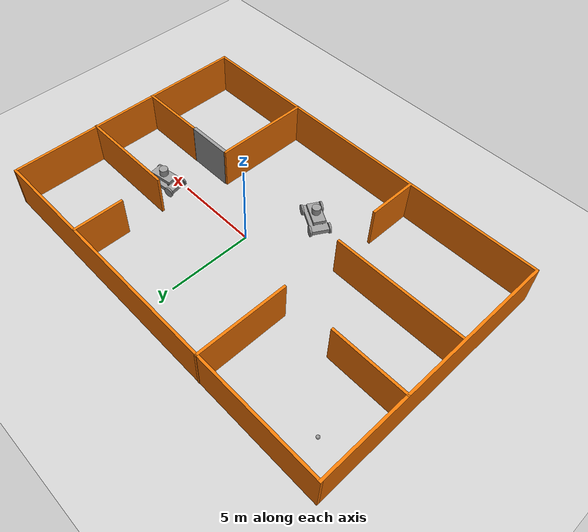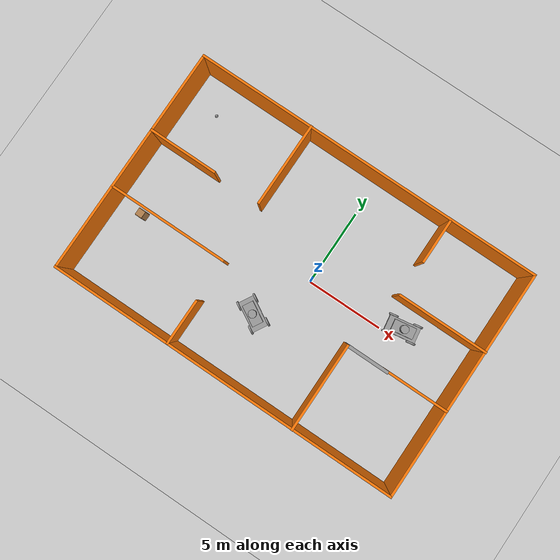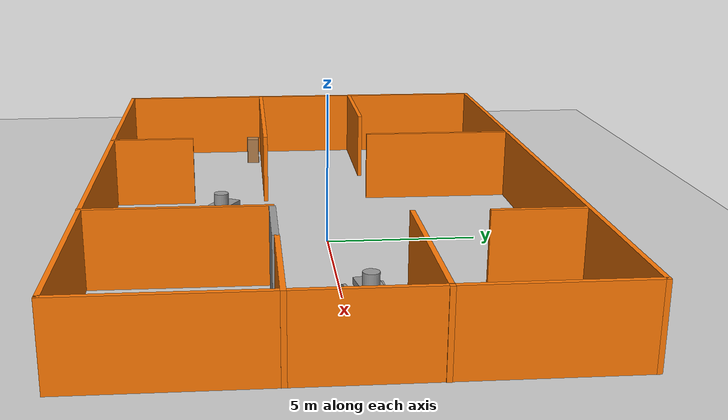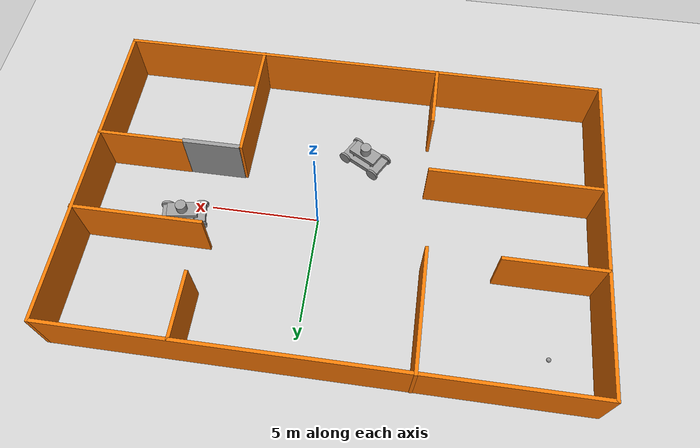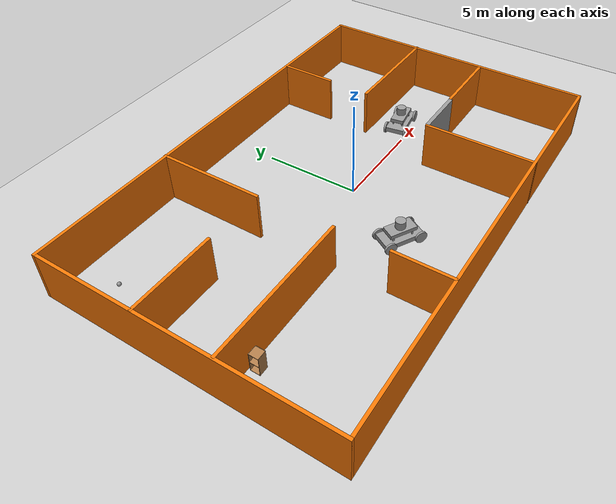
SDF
<sdf version="1.6">
 <world name="default">
  <plugin name="hello" filename="libhello.so"/>
  <light name="sun" type="directional">
   <pose>0 0 10 0 -0 0</pose>
   <diffuse>0.8 0.8 0.8 1</diffuse>
   <specular>0.2 0.2 0.2 1</specular>
   <attenuation>
    <range>1000</range>
    <constant>0.9</constant>
    <linear>0.01</linear>
    <quadratic>0.001</quadratic>
   </attenuation>
   <direction>-0.5 0.1 -0.9</direction>
   <spot><inner_angle>0</inner_angle><outer_angle>0</outer_angle><falloff>0</falloff></spot>
  </light>
  <model name="ground_plane">
   <static>1</static>
   <link name="link">
    <collision name="collision">
     <geometry><plane><normal>0 0 1</normal><size>100 100</size></plane></geometry>
     <surface>
      <contact><collide_bitmask>65535</collide_bitmask></contact>
      <friction><ode><mu>100</mu><mu2>50</mu2></ode></friction>
     </surface>
    </collision>
    <visual name="visual">
     <cast_shadows>0</cast_shadows>
     <geometry><plane><normal>0 0 1</normal><size>100 100</size></plane></geometry>
     <material>
      <script><uri>file://media/materials/scripts/gazebo.material</uri><name>Gazebo/Grey</name></script>
     </material>
    </visual>
   </link>
  </model>
  <gravity>0 0 -9.8</gravity>
  <magnetic_field>6e-06 2.3e-05 -4.2e-05</magnetic_field>
  <atmosphere type="adiabatic"/>
  <physics name="default_physics" default="0" type="ode">
   <max_step_size>0.001</max_step_size>
   <real_time_factor>1</real_time_factor>
   <real_time_update_rate>1000</real_time_update_rate>
  </physics>
  <scene><ambient>0.4 0.4 0.4 1</ambient><background>0.7 0.7 0.7 1</background><shadows>1</shadows></scene>
  <spherical_coordinates>
   <surface_model>EARTH_WGS84</surface_model>
   <latitude_deg>0</latitude_deg>
   <longitude_deg>0</longitude_deg>
   <elevation>0</elevation>
   <heading_deg>0</heading_deg>
  </spherical_coordinates>
  <model name="Quad_Robot">
   <link name="link_0">
    <inertial>
     <mass>1</mass>
     <inertia>
      <ixx>0.166667</ixx>
      <ixy>0</ixy>
      <ixz>0</ixz>
      <iyy>0.166667</iyy>
      <iyz>0</iyz>
      <izz>0.166667</izz>
     </inertia>
    </inertial>
    <pose>0.513425 -0.510943 0.328636 0 -0 0</pose>
    <visual name="visual">
     <geometry><box><size>2 1 0.25</size></box></geometry>
     <material>
      <lighting>1</lighting>
      <script><uri>file://media/materials/scripts/gazebo.material</uri><name>Gazebo/Grey</name></script>
      <shader type="pixel"><normal_map>__default__</normal_map></shader>
      <ambient>0.3 0.3 0.3 1</ambient>
      <diffuse>0.7 0.7 0.7 1</diffuse>
      <specular>0.01 0.01 0.01 1</specular>
      <emissive>0 0 0 1</emissive>
     </material>
    </visual>
    <collision name="collision">
     <geometry><box><size>2 1 0.25</size></box></geometry>
     <surface>
      <friction>
       <ode><mu>1</mu><mu2>1</mu2><fdir1>0 0 0</fdir1><slip1>0</slip1><slip2>0</slip2></ode>
       <torsional>
        <coefficient>1</coefficient>
        <patch_radius>0</patch_radius>
        <surface_radius>0</surface_radius>
        <use_patch_radius>1</use_patch_radius>
        <ode><slip>0</slip></ode>
       </torsional>
      </friction>
      <bounce><restitution_coefficient>0</restitution_coefficient><threshold>1e+06</threshold></bounce>
      <contact>
       <collide_without_contact>0</collide_without_contact>
       <collide_without_contact_bitmask>1</collide_without_contact_bitmask>
       <collide_bitmask>1</collide_bitmask>
       <ode>
        <soft_cfm>0</soft_cfm>
        <soft_erp>0.2</soft_erp>
        <kp>1e+13</kp>
        <kd>1</kd>
        <max_vel>0.01</max_vel>
        <min_depth>0</min_depth>
       </ode>
       <bullet>
        <split_impulse>1</split_impulse>
        <split_impulse_penetration_threshold>-0.01</split_impulse_penetration_threshold>
        <soft_cfm>0</soft_cfm>
        <soft_erp>0.2</soft_erp>
        <kp>1e+13</kp>
        <kd>1</kd>
       </bullet>
      </contact>
     </surface>
    </collision>
   </link>
   <link name="link_1">
    <inertial>
     <mass>1</mass>
     <inertia><ixx>0.145833</ixx><ixy>0</ixy><ixz>0</ixz><iyy>0.145833</iyy><iyz>0</iyz><izz>0.125</izz></inertia>
    </inertial>
    <pose>1.31343 0.039057 0.328636 1.575 -0 0</pose>
    <visual name="visual">
     <geometry><cylinder><radius>0.3</radius><length>0.1</length></cylinder></geometry>
     <material>
      <lighting>1</lighting>
      <script><uri>file://media/materials/scripts/gazebo.material</uri><name>Gazebo/Grey</name></script>
      <shader type="pixel"><normal_map>__default__</normal_map></shader>
      <ambient>0.3 0.3 0.3 1</ambient>
      <diffuse>0.7 0.7 0.7 1</diffuse>
      <specular>0.01 0.01 0.01 1</specular>
      <emissive>0 0 0 1</emissive>
     </material>
    </visual>
    <collision name="collision">
     <geometry><cylinder><radius>0.3</radius><length>0.1</length></cylinder></geometry>
     <surface>
      <friction>
       <ode><mu>1</mu><mu2>1</mu2><fdir1>0 0 0</fdir1><slip1>0</slip1><slip2>0</slip2></ode>
       <torsional>
        <coefficient>1</coefficient>
        <patch_radius>0</patch_radius>
        <surface_radius>0</surface_radius>
        <use_patch_radius>1</use_patch_radius>
        <ode><slip>0</slip></ode>
       </torsional>
      </friction>
      <bounce><restitution_coefficient>0</restitution_coefficient><threshold>1e+06</threshold></bounce>
      <contact>
       <collide_without_contact>0</collide_without_contact>
       <collide_without_contact_bitmask>1</collide_without_contact_bitmask>
       <collide_bitmask>1</collide_bitmask>
       <ode>
        <soft_cfm>0</soft_cfm>
        <soft_erp>0.2</soft_erp>
        <kp>1e+13</kp>
        <kd>1</kd>
        <max_vel>0.01</max_vel>
        <min_depth>0</min_depth>
       </ode>
       <bullet>
        <split_impulse>1</split_impulse>
        <split_impulse_penetration_threshold>-0.01</split_impulse_penetration_threshold>
        <soft_cfm>0</soft_cfm>
        <soft_erp>0.2</soft_erp>
        <kp>1e+13</kp>
        <kd>1</kd>
       </bullet>
      </contact>
     </surface>
    </collision>
   </link>
   <link name="link_1_clone">
    <inertial>
     <mass>1</mass>
     <inertia><ixx>0.145833</ixx><ixy>0</ixy><ixz>0</ixz><iyy>0.145833</iyy><iyz>0</iyz><izz>0.125</izz></inertia>
    </inertial>
    <pose>1.31343 -1.06094 0.328636 1.575 -0 0</pose>
    <visual name="visual">
     <geometry><cylinder><radius>0.3</radius><length>0.1</length></cylinder></geometry>
     <material>
      <lighting>1</lighting>
      <script><uri>file://media/materials/scripts/gazebo.material</uri><name>Gazebo/Grey</name></script>
      <shader type="pixel"><normal_map>__default__</normal_map></shader>
      <ambient>0.3 0.3 0.3 1</ambient>
      <diffuse>0.7 0.7 0.7 1</diffuse>
      <specular>0.01 0.01 0.01 1</specular>
      <emissive>0 0 0 1</emissive>
     </material>
    </visual>
    <collision name="collision">
     <geometry><cylinder><radius>0.3</radius><length>0.1</length></cylinder></geometry>
     <surface>
      <friction>
       <ode><mu>1</mu><mu2>1</mu2><fdir1>0 0 0</fdir1><slip1>0</slip1><slip2>0</slip2></ode>
       <torsional>
        <coefficient>1</coefficient>
        <patch_radius>0</patch_radius>
        <surface_radius>0</surface_radius>
        <use_patch_radius>1</use_patch_radius>
        <ode><slip>0</slip></ode>
       </torsional>
      </friction>
      <bounce><restitution_coefficient>0</restitution_coefficient><threshold>1e+06</threshold></bounce>
      <contact>
       <collide_without_contact>0</collide_without_contact>
       <collide_without_contact_bitmask>1</collide_without_contact_bitmask>
       <collide_bitmask>1</collide_bitmask>
       <ode>
        <soft_cfm>0</soft_cfm>
        <soft_erp>0.2</soft_erp>
        <kp>1e+13</kp>
        <kd>1</kd>
        <max_vel>0.01</max_vel>
        <min_depth>0</min_depth>
       </ode>
       <bullet>
        <split_impulse>1</split_impulse>
        <split_impulse_penetration_threshold>-0.01</split_impulse_penetration_threshold>
        <soft_cfm>0</soft_cfm>
        <soft_erp>0.2</soft_erp>
        <kp>1e+13</kp>
        <kd>1</kd>
       </bullet>
      </contact>
     </surface>
    </collision>
   </link>
   <link name="link_1_clone_0">
    <inertial>
     <mass>1</mass>
     <inertia><ixx>0.145833</ixx><ixy>0</ixy><ixz>0</ixz><iyy>0.145833</iyy><iyz>0</iyz><izz>0.125</izz></inertia>
    </inertial>
    <pose>-0.286575 0.039057 0.328636 1.575 -0 0</pose>
    <visual name="visual">
     <geometry><cylinder><radius>0.3</radius><length>0.1</length></cylinder></geometry>
     <material>
      <lighting>1</lighting>
      <script><uri>file://media/materials/scripts/gazebo.material</uri><name>Gazebo/Grey</name></script>
      <shader type="pixel"><normal_map>__default__</normal_map></shader>
      <ambient>0.3 0.3 0.3 1</ambient>
      <diffuse>0.7 0.7 0.7 1</diffuse>
      <specular>0.01 0.01 0.01 1</specular>
      <emissive>0 0 0 1</emissive>
     </material>
    </visual>
    <collision name="collision">
     <geometry><cylinder><radius>0.3</radius><length>0.1</length></cylinder></geometry>
     <surface>
      <friction>
       <ode><mu>1</mu><mu2>1</mu2><fdir1>0 0 0</fdir1><slip1>0</slip1><slip2>0</slip2></ode>
       <torsional>
        <coefficient>1</coefficient>
        <patch_radius>0</patch_radius>
        <surface_radius>0</surface_radius>
        <use_patch_radius>1</use_patch_radius>
        <ode><slip>0</slip></ode>
       </torsional>
      </friction>
      <bounce><restitution_coefficient>0</restitution_coefficient><threshold>1e+06</threshold></bounce>
      <contact>
       <collide_without_contact>0</collide_without_contact>
       <collide_without_contact_bitmask>1</collide_without_contact_bitmask>
       <collide_bitmask>1</collide_bitmask>
       <ode>
        <soft_cfm>0</soft_cfm>
        <soft_erp>0.2</soft_erp>
        <kp>1e+13</kp>
        <kd>1</kd>
        <max_vel>0.01</max_vel>
        <min_depth>0</min_depth>
       </ode>
       <bullet>
        <split_impulse>1</split_impulse>
        <split_impulse_penetration_threshold>-0.01</split_impulse_penetration_threshold>
        <soft_cfm>0</soft_cfm>
        <soft_erp>0.2</soft_erp>
        <kp>1e+13</kp>
        <kd>1</kd>
       </bullet>
      </contact>
     </surface>
    </collision>
   </link>
   <link name="link_1_clone_1">
    <inertial>
     <mass>1</mass>
     <inertia><ixx>0.145833</ixx><ixy>0</ixy><ixz>0</ixz><iyy>0.145833</iyy><iyz>0</iyz><izz>0.125</izz></inertia>
    </inertial>
    <pose>-0.286575 -1.06094 0.328636 1.575 -0 0</pose>
    <visual name="visual">
     <geometry><cylinder><radius>0.3</radius><length>0.1</length></cylinder></geometry>
     <material>
      <lighting>1</lighting>
      <script><uri>file://media/materials/scripts/gazebo.material</uri><name>Gazebo/Grey</name></script>
      <shader type="pixel"><normal_map>__default__</normal_map></shader>
      <ambient>0.3 0.3 0.3 1</ambient>
      <diffuse>0.7 0.7 0.7 1</diffuse>
      <specular>0.01 0.01 0.01 1</specular>
      <emissive>0 0 0 1</emissive>
     </material>
    </visual>
    <collision name="collision">
     <geometry><cylinder><radius>0.3</radius><length>0.1</length></cylinder></geometry>
     <surface>
      <friction>
       <ode><mu>1</mu><mu2>1</mu2><fdir1>0 0 0</fdir1><slip1>0</slip1><slip2>0</slip2></ode>
       <torsional>
        <coefficient>1</coefficient>
        <patch_radius>0</patch_radius>
        <surface_radius>0</surface_radius>
        <use_patch_radius>1</use_patch_radius>
        <ode><slip>0</slip></ode>
       </torsional>
      </friction>
      <bounce><restitution_coefficient>0</restitution_coefficient><threshold>1e+06</threshold></bounce>
      <contact>
       <collide_without_contact>0</collide_without_contact>
       <collide_without_contact_bitmask>1</collide_without_contact_bitmask>
       <collide_bitmask>1</collide_bitmask>
       <ode>
        <soft_cfm>0</soft_cfm>
        <soft_erp>0.2</soft_erp>
        <kp>1e+13</kp>
        <kd>1</kd>
        <max_vel>0.01</max_vel>
        <min_depth>0</min_depth>
       </ode>
       <bullet>
        <split_impulse>1</split_impulse>
        <split_impulse_penetration_threshold>-0.01</split_impulse_penetration_threshold>
        <soft_cfm>0</soft_cfm>
        <soft_erp>0.2</soft_erp>
        <kp>1e+13</kp>
        <kd>1</kd>
       </bullet>
      </contact>
     </surface>
    </collision>
   </link>
   <link name="link_2">
    <inertial>
     <mass>1</mass>
     <inertia><ixx>0.145833</ixx><ixy>0</ixy><ixz>0</ixz><iyy>0.145833</iyy><iyz>0</iyz><izz>0.125</izz></inertia>
    </inertial>
    <pose>1.01343 -0.260943 0.578636 0 -0 0</pose>
    <visual name="visual">
     <geometry><cylinder><radius>0.05</radius><length>0.25</length></cylinder></geometry>
     <material>
      <lighting>1</lighting>
      <script><uri>file://media/materials/scripts/gazebo.material</uri><name>Gazebo/Grey</name></script>
      <shader type="pixel"><normal_map>__default__</normal_map></shader>
      <ambient>0.3 0.3 0.3 1</ambient>
      <diffuse>0.7 0.7 0.7 1</diffuse>
      <specular>0.01 0.01 0.01 1</specular>
      <emissive>0 0 0 1</emissive>
     </material>
    </visual>
    <collision name="collision">
     <geometry><cylinder><radius>0.05</radius><length>0.25</length></cylinder></geometry>
     <surface>
      <friction>
       <ode><mu>1</mu><mu2>1</mu2><fdir1>0 0 0</fdir1><slip1>0</slip1><slip2>0</slip2></ode>
       <torsional>
        <coefficient>1</coefficient>
        <patch_radius>0</patch_radius>
        <surface_radius>0</surface_radius>
        <use_patch_radius>1</use_patch_radius>
        <ode><slip>0</slip></ode>
       </torsional>
      </friction>
      <bounce><restitution_coefficient>0</restitution_coefficient><threshold>1e+06</threshold></bounce>
      <contact>
       <collide_without_contact>0</collide_without_contact>
       <collide_without_contact_bitmask>1</collide_without_contact_bitmask>
       <collide_bitmask>1</collide_bitmask>
       <ode>
        <soft_cfm>0</soft_cfm>
        <soft_erp>0.2</soft_erp>
        <kp>1e+13</kp>
        <kd>1</kd>
        <max_vel>0.01</max_vel>
        <min_depth>0</min_depth>
       </ode>
       <bullet>
        <split_impulse>1</split_impulse>
        <split_impulse_penetration_threshold>-0.01</split_impulse_penetration_threshold>
        <soft_cfm>0</soft_cfm>
        <soft_erp>0.2</soft_erp>
        <kp>1e+13</kp>
        <kd>1</kd>
       </bullet>
      </contact>
     </surface>
    </collision>
   </link>
   <link name="link_2_clone">
    <inertial>
     <mass>1</mass>
     <inertia><ixx>0.145833</ixx><ixy>0</ixy><ixz>0</ixz><iyy>0.145833</iyy><iyz>0</iyz><izz>0.125</izz></inertia>
    </inertial>
    <pose>0.013425 -0.260943 0.578636 0 -0 0</pose>
    <visual name="visual">
     <geometry><cylinder><radius>0.05</radius><length>0.25</length></cylinder></geometry>
     <material>
      <lighting>1</lighting>
      <script><uri>file://media/materials/scripts/gazebo.material</uri><name>Gazebo/Grey</name></script>
      <shader type="pixel"><normal_map>__default__</normal_map></shader>
      <ambient>0.3 0.3 0.3 1</ambient>
      <diffuse>0.7 0.7 0.7 1</diffuse>
      <specular>0.01 0.01 0.01 1</specular>
      <emissive>0 0 0 1</emissive>
     </material>
    </visual>
    <collision name="collision">
     <geometry><cylinder><radius>0.05</radius><length>0.25</length></cylinder></geometry>
     <surface>
      <friction>
       <ode><mu>1</mu><mu2>1</mu2><fdir1>0 0 0</fdir1><slip1>0</slip1><slip2>0</slip2></ode>
       <torsional>
        <coefficient>1</coefficient>
        <patch_radius>0</patch_radius>
        <surface_radius>0</surface_radius>
        <use_patch_radius>1</use_patch_radius>
        <ode><slip>0</slip></ode>
       </torsional>
      </friction>
      <bounce><restitution_coefficient>0</restitution_coefficient><threshold>1e+06</threshold></bounce>
      <contact>
       <collide_without_contact>0</collide_without_contact>
       <collide_without_contact_bitmask>1</collide_without_contact_bitmask>
       <collide_bitmask>1</collide_bitmask>
       <ode>
        <soft_cfm>0</soft_cfm>
        <soft_erp>0.2</soft_erp>
        <kp>1e+13</kp>
        <kd>1</kd>
        <max_vel>0.01</max_vel>
        <min_depth>0</min_depth>
       </ode>
       <bullet>
        <split_impulse>1</split_impulse>
        <split_impulse_penetration_threshold>-0.01</split_impulse_penetration_threshold>
        <soft_cfm>0</soft_cfm>
        <soft_erp>0.2</soft_erp>
        <kp>1e+13</kp>
        <kd>1</kd>
       </bullet>
      </contact>
     </surface>
    </collision>
   </link>
   <link name="link_2_clone_0">
    <inertial>
     <mass>1</mass>
     <inertia><ixx>0.145833</ixx><ixy>0</ixy><ixz>0</ixz><iyy>0.145833</iyy><iyz>0</iyz><izz>0.125</izz></inertia>
    </inertial>
    <pose>1.01343 -0.760943 0.578636 0 -0 0</pose>
    <visual name="visual">
     <geometry><cylinder><radius>0.05</radius><length>0.25</length></cylinder></geometry>
     <material>
      <lighting>1</lighting>
      <script><uri>file://media/materials/scripts/gazebo.material</uri><name>Gazebo/Grey</name></script>
      <shader type="pixel"><normal_map>__default__</normal_map></shader>
      <ambient>0.3 0.3 0.3 1</ambient>
      <diffuse>0.7 0.7 0.7 1</diffuse>
      <specular>0.01 0.01 0.01 1</specular>
      <emissive>0 0 0 1</emissive>
     </material>
    </visual>
    <collision name="collision">
     <geometry><cylinder><radius>0.05</radius><length>0.25</length></cylinder></geometry>
     <surface>
      <friction>
       <ode><mu>1</mu><mu2>1</mu2><fdir1>0 0 0</fdir1><slip1>0</slip1><slip2>0</slip2></ode>
       <torsional>
        <coefficient>1</coefficient>
        <patch_radius>0</patch_radius>
        <surface_radius>0</surface_radius>
        <use_patch_radius>1</use_patch_radius>
        <ode><slip>0</slip></ode>
       </torsional>
      </friction>
      <bounce><restitution_coefficient>0</restitution_coefficient><threshold>1e+06</threshold></bounce>
      <contact>
       <collide_without_contact>0</collide_without_contact>
       <collide_without_contact_bitmask>1</collide_without_contact_bitmask>
       <collide_bitmask>1</collide_bitmask>
       <ode>
        <soft_cfm>0</soft_cfm>
        <soft_erp>0.2</soft_erp>
        <kp>1e+13</kp>
        <kd>1</kd>
        <max_vel>0.01</max_vel>
        <min_depth>0</min_depth>
       </ode>
       <bullet>
        <split_impulse>1</split_impulse>
        <split_impulse_penetration_threshold>-0.01</split_impulse_penetration_threshold>
        <soft_cfm>0</soft_cfm>
        <soft_erp>0.2</soft_erp>
        <kp>1e+13</kp>
        <kd>1</kd>
       </bullet>
      </contact>
     </surface>
    </collision>
   </link>
   <link name="link_2_clone_1">
    <inertial>
     <mass>1</mass>
     <inertia><ixx>0.145833</ixx><ixy>0</ixy><ixz>0</ixz><iyy>0.145833</iyy><iyz>0</iyz><izz>0.125</izz></inertia>
    </inertial>
    <pose>0.013425 -0.760943 0.578636 0 -0 0</pose>
    <visual name="visual">
     <geometry><cylinder><radius>0.05</radius><length>0.25</length></cylinder></geometry>
     <material>
      <lighting>1</lighting>
      <script><uri>file://media/materials/scripts/gazebo.material</uri><name>Gazebo/Grey</name></script>
      <shader type="pixel"><normal_map>__default__</normal_map></shader>
      <ambient>0.3 0.3 0.3 1</ambient>
      <diffuse>0.7 0.7 0.7 1</diffuse>
      <specular>0.01 0.01 0.01 1</specular>
      <emissive>0 0 0 1</emissive>
     </material>
    </visual>
    <collision name="collision">
     <geometry><cylinder><radius>0.05</radius><length>0.25</length></cylinder></geometry>
     <surface>
      <friction>
       <ode><mu>1</mu><mu2>1</mu2><fdir1>0 0 0</fdir1><slip1>0</slip1><slip2>0</slip2></ode>
       <torsional>
        <coefficient>1</coefficient>
        <patch_radius>0</patch_radius>
        <surface_radius>0</surface_radius>
        <use_patch_radius>1</use_patch_radius>
        <ode><slip>0</slip></ode>
       </torsional>
      </friction>
      <bounce><restitution_coefficient>0</restitution_coefficient><threshold>1e+06</threshold></bounce>
      <contact>
       <collide_without_contact>0</collide_without_contact>
       <collide_without_contact_bitmask>1</collide_without_contact_bitmask>
       <collide_bitmask>1</collide_bitmask>
       <ode>
        <soft_cfm>0</soft_cfm>
        <soft_erp>0.2</soft_erp>
        <kp>1e+13</kp>
        <kd>1</kd>
        <max_vel>0.01</max_vel>
        <min_depth>0</min_depth>
       </ode>
       <bullet>
        <split_impulse>1</split_impulse>
        <split_impulse_penetration_threshold>-0.01</split_impulse_penetration_threshold>
        <soft_cfm>0</soft_cfm>
        <soft_erp>0.2</soft_erp>
        <kp>1e+13</kp>
        <kd>1</kd>
       </bullet>
      </contact>
     </surface>
    </collision>
   </link>
   <link name="link_3">
    <inertial>
     <mass>1</mass>
     <inertia>
      <ixx>0.166667</ixx>
      <ixy>0</ixy>
      <ixz>0</ixz>
      <iyy>0.166667</iyy>
      <iyz>0</iyz>
      <izz>0.166667</izz>
     </inertia>
    </inertial>
    <pose>0.513425 -0.510941 0.773636 0 -0 0</pose>
    <visual name="visual">
     <geometry><box><size>1.4 0.7 0.2</size></box></geometry>
     <material>
      <lighting>1</lighting>
      <script><uri>file://media/materials/scripts/gazebo.material</uri><name>Gazebo/Grey</name></script>
      <shader type="pixel"><normal_map>__default__</normal_map></shader>
      <ambient>0.3 0.3 0.3 1</ambient>
      <diffuse>0.7 0.7 0.7 1</diffuse>
      <specular>0.01 0.01 0.01 1</specular>
      <emissive>0 0 0 1</emissive>
     </material>
    </visual>
    <collision name="collision">
     <geometry><box><size>1.4 0.7 0.2</size></box></geometry>
     <surface>
      <friction>
       <ode><mu>1</mu><mu2>1</mu2><fdir1>0 0 0</fdir1><slip1>0</slip1><slip2>0</slip2></ode>
       <torsional>
        <coefficient>1</coefficient>
        <patch_radius>0</patch_radius>
        <surface_radius>0</surface_radius>
        <use_patch_radius>1</use_patch_radius>
        <ode><slip>0</slip></ode>
       </torsional>
      </friction>
      <bounce><restitution_coefficient>0</restitution_coefficient><threshold>1e+06</threshold></bounce>
      <contact>
       <collide_without_contact>0</collide_without_contact>
       <collide_without_contact_bitmask>1</collide_without_contact_bitmask>
       <collide_bitmask>1</collide_bitmask>
       <ode>
        <soft_cfm>0</soft_cfm>
        <soft_erp>0.2</soft_erp>
        <kp>1e+13</kp>
        <kd>1</kd>
        <max_vel>0.01</max_vel>
        <min_depth>0</min_depth>
       </ode>
       <bullet>
        <split_impulse>1</split_impulse>
        <split_impulse_penetration_threshold>-0.01</split_impulse_penetration_threshold>
        <soft_cfm>0</soft_cfm>
        <soft_erp>0.2</soft_erp>
        <kp>1e+13</kp>
        <kd>1</kd>
       </bullet>
      </contact>
     </surface>
    </collision>
   </link>
   <link name="link_4">
    <inertial>
     <mass>1</mass>
     <inertia><ixx>0.145833</ixx><ixy>0</ixy><ixz>0</ixz><iyy>0.145833</iyy><iyz>0</iyz><izz>0.125</izz></inertia>
    </inertial>
    <pose>0.513425 -0.510941 1.07364 0 -0 0</pose>
    <visual name="visual">
     <geometry><cylinder><radius>0.25</radius><length>0.4</length></cylinder></geometry>
     <material>
      <lighting>1</lighting>
      <script><uri>file://media/materials/scripts/gazebo.material</uri><name>Gazebo/Grey</name></script>
      <shader type="pixel"><normal_map>__default__</normal_map></shader>
      <ambient>0.3 0.3 0.3 1</ambient>
      <diffuse>0.7 0.7 0.7 1</diffuse>
      <specular>0.01 0.01 0.01 1</specular>
      <emissive>0 0 0 1</emissive>
     </material>
    </visual>
    <collision name="collision">
     <geometry><cylinder><radius>0.25</radius><length>0.4</length></cylinder></geometry>
     <surface>
      <friction>
       <ode><mu>1</mu><mu2>1</mu2><fdir1>0 0 0</fdir1><slip1>0</slip1><slip2>0</slip2></ode>
       <torsional>
        <coefficient>1</coefficient>
        <patch_radius>0</patch_radius>
        <surface_radius>0</surface_radius>
        <use_patch_radius>1</use_patch_radius>
        <ode><slip>0</slip></ode>
       </torsional>
      </friction>
      <bounce><restitution_coefficient>0</restitution_coefficient><threshold>1e+06</threshold></bounce>
      <contact>
       <collide_without_contact>0</collide_without_contact>
       <collide_without_contact_bitmask>1</collide_without_contact_bitmask>
       <collide_bitmask>1</collide_bitmask>
       <ode>
        <soft_cfm>0</soft_cfm>
        <soft_erp>0.2</soft_erp>
        <kp>1e+13</kp>
        <kd>1</kd>
        <max_vel>0.01</max_vel>
        <min_depth>0</min_depth>
       </ode>
       <bullet>
        <split_impulse>1</split_impulse>
        <split_impulse_penetration_threshold>-0.01</split_impulse_penetration_threshold>
        <soft_cfm>0</soft_cfm>
        <soft_erp>0.2</soft_erp>
        <kp>1e+13</kp>
        <kd>1</kd>
       </bullet>
      </contact>
     </surface>
    </collision>
   </link>
   <joint name="link_0_JOINT_0" type="revolute">
    <parent>link_0</parent>
    <child>link_1</child>
    <axis>
     <xyz>0 0 1</xyz>
     <limit>
      <lower>-1.79769e+308</lower>
      <upper>1.79769e+308</upper>
      <effort>-1</effort>
      <velocity>-1</velocity>
     </limit>
     <dynamics>
      <spring_reference>0</spring_reference>
      <spring_stiffness>0</spring_stiffness>
      <damping>0</damping>
     </dynamics>
     <use_parent_model_frame>0</use_parent_model_frame>
    </axis>
    <physics>
     <ode><limit><cfm>0</cfm><erp>0.2</erp></limit><suspension><cfm>0</cfm><erp>0.2</erp></suspension></ode>
    </physics>
   </joint>
   <joint name="link_0_JOINT_1" type="revolute">
    <parent>link_0</parent>
    <child>link_1_clone</child>
    <axis>
     <xyz>0 0 1</xyz>
     <limit>
      <lower>-1.79769e+308</lower>
      <upper>1.79769e+308</upper>
      <effort>-1</effort>
      <velocity>-1</velocity>
     </limit>
     <dynamics>
      <spring_reference>0</spring_reference>
      <spring_stiffness>0</spring_stiffness>
      <damping>0</damping>
     </dynamics>
     <use_parent_model_frame>0</use_parent_model_frame>
    </axis>
    <physics>
     <ode><limit><cfm>0</cfm><erp>0.2</erp></limit><suspension><cfm>0</cfm><erp>0.2</erp></suspension></ode>
    </physics>
   </joint>
   <joint name="link_0_JOINT_2" type="revolute">
    <parent>link_0</parent>
    <child>link_1_clone_0</child>
    <axis>
     <xyz>0 0 1</xyz>
     <limit>
      <lower>-1.79769e+308</lower>
      <upper>1.79769e+308</upper>
      <effort>-1</effort>
      <velocity>-1</velocity>
     </limit>
     <dynamics>
      <spring_reference>0</spring_reference>
      <spring_stiffness>0</spring_stiffness>
      <damping>0</damping>
     </dynamics>
     <use_parent_model_frame>0</use_parent_model_frame>
    </axis>
    <physics>
     <ode><limit><cfm>0</cfm><erp>0.2</erp></limit><suspension><cfm>0</cfm><erp>0.2</erp></suspension></ode>
    </physics>
   </joint>
   <joint name="link_0_JOINT_3" type="revolute">
    <parent>link_0</parent>
    <child>link_1_clone_1</child>
    <axis>
     <xyz>0 0 1</xyz>
     <limit>
      <lower>-1.79769e+308</lower>
      <upper>1.79769e+308</upper>
      <effort>-1</effort>
      <velocity>-1</velocity>
     </limit>
     <dynamics>
      <spring_reference>0</spring_reference>
      <spring_stiffness>0</spring_stiffness>
      <damping>0</damping>
     </dynamics>
     <use_parent_model_frame>0</use_parent_model_frame>
    </axis>
    <physics>
     <ode><limit><cfm>0</cfm><erp>0.2</erp></limit><suspension><cfm>0</cfm><erp>0.2</erp></suspension></ode>
    </physics>
   </joint>
   <joint name="link_0_JOINT_4" type="fixed">
    <parent>link_0</parent>
    <child>link_2</child>
    <physics>
     <ode><limit><cfm>0</cfm><erp>0.2</erp></limit><suspension><cfm>0</cfm><erp>0.2</erp></suspension></ode>
    </physics>
   </joint>
   <joint name="link_0_JOINT_5" type="fixed">
    <parent>link_0</parent>
    <child>link_2_clone</child>
    <physics>
     <ode><limit><cfm>0</cfm><erp>0.2</erp></limit><suspension><cfm>0</cfm><erp>0.2</erp></suspension></ode>
    </physics>
   </joint>
   <joint name="link_0_JOINT_6" type="fixed">
    <parent>link_0</parent>
    <child>link_2_clone_0</child>
    <physics>
     <ode><limit><cfm>0</cfm><erp>0.2</erp></limit><suspension><cfm>0</cfm><erp>0.2</erp></suspension></ode>
    </physics>
   </joint>
   <joint name="link_0_JOINT_7" type="fixed">
    <parent>link_0</parent>
    <child>link_2_clone_1</child>
    <physics>
     <ode><limit><cfm>0</cfm><erp>0.2</erp></limit><suspension><cfm>0</cfm><erp>0.2</erp></suspension></ode>
    </physics>
   </joint>
   <joint name="link_0_JOINT_8" type="fixed">
    <parent>link_0</parent>
    <child>link_3</child>
    <physics>
     <ode><limit><cfm>0</cfm><erp>0.2</erp></limit><suspension><cfm>0</cfm><erp>0.2</erp></suspension></ode>
    </physics>
   </joint>
   <joint name="link_3_JOINT_9" type="fixed">
    <parent>link_3</parent>
    <child>link_4</child>
    <physics>
     <ode><limit><cfm>0</cfm><erp>0.2</erp></limit><suspension><cfm>0</cfm><erp>0.2</erp></suspension></ode>
    </physics>
   </joint>
   <static>0</static>
   <pose>-1.97132 -2.86284 -0.028429 -1e-06 -1e-06 -0.516337</pose>
  </model>
  <model name="Office_Building">
   <pose>-1.04008 -0.12188 0 0 -0 0</pose>
   <link name="Door_0">
    <collision name="Door_0_Collision">
     <geometry><box><size>2.67045 0.2 2.5</size></box></geometry>
     <pose>0 0 1.25 0 -0 0</pose>
    </collision>
    <visual name="Door_0_Visual">
     <pose>0 0 1.25 0 -0 0</pose>
     <geometry><box><size>2.67045 0.2 2.5</size></box></geometry>
     <material>
      <script><uri>file://media/materials/scripts/gazebo.material</uri><name>Gazebo/Grey</name></script>
     </material>
    </visual>
    <pose>6.19538 -1.827 0 0 -0 0</pose>
   </link>
   <link name="Wall_11">
    <collision name="Wall_11_Collision">
     <geometry><box><size>7.75 0.15 2.5</size></box></geometry>
     <pose>0 0 1.25 0 -0 0</pose>
    </collision>
    <visual name="Wall_11_Visual">
     <pose>0 0 1.25 0 -0 0</pose>
     <geometry><box><size>7.75 0.15 2.5</size></box></geometry>
     <material>
      <script><uri>file://media/materials/scripts/gazebo.material</uri><name>Gazebo/Grey</name></script>
      <ambient>0.996078 0.47451 0.0196078 1</ambient>
     </material>
     <meta><layer>0</layer></meta>
    </visual>
    <pose>-7.57322 -1.8119 0 0 -0 3.14159</pose>
   </link>
   <link name="Wall_14">
    <collision name="Wall_14_Collision">
     <geometry><box><size>5.5 0.15 2.5</size></box></geometry>
     <pose>0 0 1.25 0 -0 0</pose>
    </collision>
    <visual name="Wall_14_Visual">
     <pose>0 0 1.25 0 -0 0</pose>
     <geometry><box><size>5.5 0.15 2.5</size></box></geometry>
     <material>
      <script><uri>file://media/materials/scripts/gazebo.material</uri><name>Gazebo/Grey</name></script>
      <ambient>0.996078 0.47451 0.0196078 1</ambient>
     </material>
     <meta><layer>0</layer></meta>
    </visual>
    <pose>-3.92743 4.76535 0 0 -0 -1.5708</pose>
   </link>
   <link name="Wall_16">
    <collision name="Wall_16_Collision">
     <geometry><box><size>4.5 0.15 2.5</size></box></geometry>
     <pose>0 0 1.25 0 -0 0</pose>
    </collision>
    <visual name="Wall_16_Visual">
     <pose>0 0 1.25 0 -0 0</pose>
     <geometry><box><size>4.5 0.15 2.5</size></box></geometry>
     <material>
      <script><uri>file://media/materials/scripts/gazebo.material</uri><name>Gazebo/Grey</name></script>
      <ambient>0.996078 0.47451 0.0196078 1</ambient>
     </material>
     <meta><layer>0</layer></meta>
    </visual>
    <pose>-9.25703 2.12031 0 0 -0 0</pose>
   </link>
   <link name="Wall_18">
    <collision name="Wall_18_Collision">
     <geometry><box><size>3 0.15 2.5</size></box></geometry>
     <pose>0 0 1.25 0 -0 0</pose>
    </collision>
    <visual name="Wall_18_Visual">
     <pose>0 0 1.25 0 -0 0</pose>
     <geometry><box><size>3 0.15 2.5</size></box></geometry>
     <material>
      <script><uri>file://media/materials/scripts/gazebo.material</uri><name>Gazebo/Grey</name></script>
      <ambient>0.996078 0.47451 0.0196078 1</ambient>
     </material>
     <meta><layer>0</layer></meta>
    </visual>
    <pose>5.73603 5.96394 0 0 -0 -1.5708</pose>
   </link>
   <link name="Wall_20">
    <collision name="Wall_20_Collision">
     <geometry><box><size>5.9 0.15 2.5</size></box></geometry>
     <pose>0 0 1.25 0 -0 0</pose>
    </collision>
    <visual name="Wall_20_Visual">
     <pose>0 0 1.25 0 -0 0</pose>
     <geometry><box><size>5.9 0.15 2.5</size></box></geometry>
     <material>
      <script><uri>file://media/materials/scripts/gazebo.material</uri><name>Gazebo/Grey</name></script>
      <ambient>0.996078 0.47451 0.0196078 1</ambient>
     </material>
     <meta><layer>0</layer></meta>
    </visual>
    <pose>8.56658 2.19741 0 0 -0 3.14159</pose>
   </link>
   <link name="Wall_22">
    <collision name="Wall_22_Collision">
     <geometry><box><size>5.75 0.15 2.5</size></box></geometry>
     <pose>0 0 1.25 0 -0 0</pose>
    </collision>
    <visual name="Wall_22_Visual">
     <pose>0 0 1.25 0 -0 0</pose>
     <geometry><box><size>5.75 0.15 2.5</size></box></geometry>
     <material>
      <script><uri>file://media/materials/scripts/gazebo.material</uri><name>Gazebo/Grey</name></script>
      <ambient>0.996078 0.47451 0.0196078 1</ambient>
     </material>
     <meta><layer>0</layer></meta>
    </visual>
    <pose>4.8108 -4.64035 0 0 -0 1.5708</pose>
   </link>
   <link name="Wall_25">
    <collision name="Wall_25_Collision">
     <geometry><box><size>4 0.15 2.5</size></box></geometry>
     <pose>0 0 1.25 0 -0 0</pose>
    </collision>
    <visual name="Wall_25_Visual">
     <pose>0 0 1.25 0 -0 0</pose>
     <geometry><box><size>4 0.15 2.5</size></box></geometry>
     <material>
      <script><uri>file://media/materials/scripts/gazebo.material</uri><name>Gazebo/Grey</name></script>
      <ambient>0.996078 0.47451 0.0196078 1</ambient>
     </material>
     <meta><layer>0</layer></meta>
    </visual>
    <pose>9.49088 -1.7862 0 0 -0 3.14159</pose>
   </link>
   <link name="Wall_4">
    <collision name="Wall_4_Collision">
     <geometry><box><size>15 0.15 2.5</size></box></geometry>
     <pose>0 0 1.25 0 -0 0</pose>
    </collision>
    <visual name="Wall_4_Visual">
     <pose>0 0 1.25 0 -0 0</pose>
     <geometry><box><size>15 0.15 2.5</size></box></geometry>
     <material>
      <script><uri>file://media/materials/scripts/gazebo.material</uri><name>Gazebo/Grey</name></script>
      <ambient>0.996078 0.47451 0.0196078 1</ambient>
     </material>
     <meta><layer>0</layer></meta>
    </visual>
    <pose>-11.4416 -0.003071 0 0 -0 -1.5708</pose>
   </link>
   <link name="Wall_5">
    <collision name="Wall_5_Collision">
     <geometry><box><size>23 0.15 2.5</size></box></geometry>
     <pose>0 0 1.25 0 -0 0</pose>
    </collision>
    <visual name="Wall_5_Visual">
     <pose>0 0 1.25 0 -0 0</pose>
     <geometry><box><size>23 0.15 2.5</size></box></geometry>
     <material>
      <script><uri>file://media/materials/scripts/gazebo.material</uri><name>Gazebo/Grey</name></script>
      <ambient>0.996078 0.47451 0.0196078 1</ambient>
     </material>
     <meta><layer>0</layer></meta>
    </visual>
    <pose>-0.016577 -7.42807 0 0 -0 0</pose>
   </link>
   <link name="Wall_6">
    <collision name="Wall_6_Collision">
     <geometry><box><size>15 0.15 2.5</size></box></geometry>
     <pose>0 0 1.25 0 -0 0</pose>
    </collision>
    <visual name="Wall_6_Visual">
     <pose>0 0 1.25 0 -0 0</pose>
     <geometry><box><size>15 0.15 2.5</size></box></geometry>
     <material>
      <script><uri>file://media/materials/scripts/gazebo.material</uri><name>Gazebo/Grey</name></script>
      <ambient>0.996078 0.47451 0.0196078 1</ambient>
     </material>
     <meta><layer>0</layer></meta>
    </visual>
    <pose>11.4084 -0.003071 0 0 -0 1.5708</pose>
   </link>
   <link name="Wall_7">
    <collision name="Wall_7_Collision">
     <geometry><box><size>23 0.15 2.5</size></box></geometry>
     <pose>0 0 1.25 0 -0 0</pose>
    </collision>
    <visual name="Wall_7_Visual">
     <pose>0 0 1.25 0 -0 0</pose>
     <geometry><box><size>23 0.15 2.5</size></box></geometry>
     <material>
      <script><uri>file://media/materials/scripts/gazebo.material</uri><name>Gazebo/Grey</name></script>
      <ambient>0.996078 0.47451 0.0196078 1</ambient>
     </material>
     <meta><layer>0</layer></meta>
    </visual>
    <pose>-0.016577 7.42193 0 0 -0 3.14159</pose>
   </link>
   <link name="Wall_9">
    <collision name="Wall_9_Collision">
     <geometry><box><size>3 0.15 2.5</size></box></geometry>
     <pose>0 0 1.25 0 -0 0</pose>
    </collision>
    <visual name="Wall_9_Visual">
     <pose>0 0 1.25 0 -0 0</pose>
     <geometry><box><size>3 0.15 2.5</size></box></geometry>
     <material>
      <script><uri>file://media/materials/scripts/gazebo.material</uri><name>Gazebo/Grey</name></script>
      <ambient>0.996078 0.47451 0.0196078 1</ambient>
     </material>
     <meta><layer>0</layer></meta>
    </visual>
    <pose>-3.69612 -5.98965 0 0 -0 1.5708</pose>
   </link>
   <static>1</static>
  </model>
  <model name="Quad_Robot_0">
   <link name="link_0">
    <inertial>
     <mass>1</mass>
     <inertia>
      <ixx>0.166667</ixx>
      <ixy>0</ixy>
      <ixz>0</ixz>
      <iyy>0.166667</iyy>
      <iyz>0</iyz>
      <izz>0.166667</izz>
     </inertia>
    </inertial>
    <pose>0.513425 -0.510943 0.328636 0 -0 0</pose>
    <visual name="visual">
     <geometry><box><size>2 1 0.25</size></box></geometry>
     <material>
      <lighting>1</lighting>
      <script><uri>file://media/materials/scripts/gazebo.material</uri><name>Gazebo/Grey</name></script>
      <shader type="pixel"><normal_map>__default__</normal_map></shader>
      <ambient>0.3 0.3 0.3 1</ambient>
      <diffuse>0.7 0.7 0.7 1</diffuse>
      <specular>0.01 0.01 0.01 1</specular>
      <emissive>0 0 0 1</emissive>
     </material>
    </visual>
    <collision name="collision">
     <geometry><box><size>2 1 0.25</size></box></geometry>
     <surface>
      <friction>
       <ode><mu>1</mu><mu2>1</mu2><fdir1>0 0 0</fdir1><slip1>0</slip1><slip2>0</slip2></ode>
       <torsional>
        <coefficient>1</coefficient>
        <patch_radius>0</patch_radius>
        <surface_radius>0</surface_radius>
        <use_patch_radius>1</use_patch_radius>
        <ode><slip>0</slip></ode>
       </torsional>
      </friction>
      <bounce><restitution_coefficient>0</restitution_coefficient><threshold>1e+06</threshold></bounce>
      <contact>
       <collide_without_contact>0</collide_without_contact>
       <collide_without_contact_bitmask>1</collide_without_contact_bitmask>
       <collide_bitmask>1</collide_bitmask>
       <ode>
        <soft_cfm>0</soft_cfm>
        <soft_erp>0.2</soft_erp>
        <kp>1e+13</kp>
        <kd>1</kd>
        <max_vel>0.01</max_vel>
        <min_depth>0</min_depth>
       </ode>
       <bullet>
        <split_impulse>1</split_impulse>
        <split_impulse_penetration_threshold>-0.01</split_impulse_penetration_threshold>
        <soft_cfm>0</soft_cfm>
        <soft_erp>0.2</soft_erp>
        <kp>1e+13</kp>
        <kd>1</kd>
       </bullet>
      </contact>
     </surface>
    </collision>
   </link>
   <link name="link_1">
    <inertial>
     <mass>1</mass>
     <inertia><ixx>0.145833</ixx><ixy>0</ixy><ixz>0</ixz><iyy>0.145833</iyy><iyz>0</iyz><izz>0.125</izz></inertia>
    </inertial>
    <pose>1.31343 0.039057 0.328636 1.575 -0 0</pose>
    <visual name="visual">
     <geometry><cylinder><radius>0.3</radius><length>0.1</length></cylinder></geometry>
     <material>
      <lighting>1</lighting>
      <script><uri>file://media/materials/scripts/gazebo.material</uri><name>Gazebo/Grey</name></script>
      <shader type="pixel"><normal_map>__default__</normal_map></shader>
      <ambient>0.3 0.3 0.3 1</ambient>
      <diffuse>0.7 0.7 0.7 1</diffuse>
      <specular>0.01 0.01 0.01 1</specular>
      <emissive>0 0 0 1</emissive>
     </material>
    </visual>
    <collision name="collision">
     <geometry><cylinder><radius>0.3</radius><length>0.1</length></cylinder></geometry>
     <surface>
      <friction>
       <ode><mu>1</mu><mu2>1</mu2><fdir1>0 0 0</fdir1><slip1>0</slip1><slip2>0</slip2></ode>
       <torsional>
        <coefficient>1</coefficient>
        <patch_radius>0</patch_radius>
        <surface_radius>0</surface_radius>
        <use_patch_radius>1</use_patch_radius>
        <ode><slip>0</slip></ode>
       </torsional>
      </friction>
      <bounce><restitution_coefficient>0</restitution_coefficient><threshold>1e+06</threshold></bounce>
      <contact>
       <collide_without_contact>0</collide_without_contact>
       <collide_without_contact_bitmask>1</collide_without_contact_bitmask>
       <collide_bitmask>1</collide_bitmask>
       <ode>
        <soft_cfm>0</soft_cfm>
        <soft_erp>0.2</soft_erp>
        <kp>1e+13</kp>
        <kd>1</kd>
        <max_vel>0.01</max_vel>
        <min_depth>0</min_depth>
       </ode>
       <bullet>
        <split_impulse>1</split_impulse>
        <split_impulse_penetration_threshold>-0.01</split_impulse_penetration_threshold>
        <soft_cfm>0</soft_cfm>
        <soft_erp>0.2</soft_erp>
        <kp>1e+13</kp>
        <kd>1</kd>
       </bullet>
      </contact>
     </surface>
    </collision>
   </link>
   <link name="link_1_clone">
    <inertial>
     <mass>1</mass>
     <inertia><ixx>0.145833</ixx><ixy>0</ixy><ixz>0</ixz><iyy>0.145833</iyy><iyz>0</iyz><izz>0.125</izz></inertia>
    </inertial>
    <pose>1.31343 -1.06094 0.328636 1.575 -0 0</pose>
    <visual name="visual">
     <geometry><cylinder><radius>0.3</radius><length>0.1</length></cylinder></geometry>
     <material>
      <lighting>1</lighting>
      <script><uri>file://media/materials/scripts/gazebo.material</uri><name>Gazebo/Grey</name></script>
      <shader type="pixel"><normal_map>__default__</normal_map></shader>
      <ambient>0.3 0.3 0.3 1</ambient>
      <diffuse>0.7 0.7 0.7 1</diffuse>
      <specular>0.01 0.01 0.01 1</specular>
      <emissive>0 0 0 1</emissive>
     </material>
    </visual>
    <collision name="collision">
     <geometry><cylinder><radius>0.3</radius><length>0.1</length></cylinder></geometry>
     <surface>
      <friction>
       <ode><mu>1</mu><mu2>1</mu2><fdir1>0 0 0</fdir1><slip1>0</slip1><slip2>0</slip2></ode>
       <torsional>
        <coefficient>1</coefficient>
        <patch_radius>0</patch_radius>
        <surface_radius>0</surface_radius>
        <use_patch_radius>1</use_patch_radius>
        <ode><slip>0</slip></ode>
       </torsional>
      </friction>
      <bounce><restitution_coefficient>0</restitution_coefficient><threshold>1e+06</threshold></bounce>
      <contact>
       <collide_without_contact>0</collide_without_contact>
       <collide_without_contact_bitmask>1</collide_without_contact_bitmask>
       <collide_bitmask>1</collide_bitmask>
       <ode>
        <soft_cfm>0</soft_cfm>
        <soft_erp>0.2</soft_erp>
        <kp>1e+13</kp>
        <kd>1</kd>
        <max_vel>0.01</max_vel>
        <min_depth>0</min_depth>
       </ode>
       <bullet>
        <split_impulse>1</split_impulse>
        <split_impulse_penetration_threshold>-0.01</split_impulse_penetration_threshold>
        <soft_cfm>0</soft_cfm>
        <soft_erp>0.2</soft_erp>
        <kp>1e+13</kp>
        <kd>1</kd>
       </bullet>
      </contact>
     </surface>
    </collision>
   </link>
   <link name="link_1_clone_0">
    <inertial>
     <mass>1</mass>
     <inertia><ixx>0.145833</ixx><ixy>0</ixy><ixz>0</ixz><iyy>0.145833</iyy><iyz>0</iyz><izz>0.125</izz></inertia>
    </inertial>
    <pose>-0.286575 0.039057 0.328636 1.575 -0 0</pose>
    <visual name="visual">
     <geometry><cylinder><radius>0.3</radius><length>0.1</length></cylinder></geometry>
     <material>
      <lighting>1</lighting>
      <script><uri>file://media/materials/scripts/gazebo.material</uri><name>Gazebo/Grey</name></script>
      <shader type="pixel"><normal_map>__default__</normal_map></shader>
      <ambient>0.3 0.3 0.3 1</ambient>
      <diffuse>0.7 0.7 0.7 1</diffuse>
      <specular>0.01 0.01 0.01 1</specular>
      <emissive>0 0 0 1</emissive>
     </material>
    </visual>
    <collision name="collision">
     <geometry><cylinder><radius>0.3</radius><length>0.1</length></cylinder></geometry>
     <surface>
      <friction>
       <ode><mu>1</mu><mu2>1</mu2><fdir1>0 0 0</fdir1><slip1>0</slip1><slip2>0</slip2></ode>
       <torsional>
        <coefficient>1</coefficient>
        <patch_radius>0</patch_radius>
        <surface_radius>0</surface_radius>
        <use_patch_radius>1</use_patch_radius>
        <ode><slip>0</slip></ode>
       </torsional>
      </friction>
      <bounce><restitution_coefficient>0</restitution_coefficient><threshold>1e+06</threshold></bounce>
      <contact>
       <collide_without_contact>0</collide_without_contact>
       <collide_without_contact_bitmask>1</collide_without_contact_bitmask>
       <collide_bitmask>1</collide_bitmask>
       <ode>
        <soft_cfm>0</soft_cfm>
        <soft_erp>0.2</soft_erp>
        <kp>1e+13</kp>
        <kd>1</kd>
        <max_vel>0.01</max_vel>
        <min_depth>0</min_depth>
       </ode>
       <bullet>
        <split_impulse>1</split_impulse>
        <split_impulse_penetration_threshold>-0.01</split_impulse_penetration_threshold>
        <soft_cfm>0</soft_cfm>
        <soft_erp>0.2</soft_erp>
        <kp>1e+13</kp>
        <kd>1</kd>
       </bullet>
      </contact>
     </surface>
    </collision>
   </link>
   <link name="link_1_clone_1">
    <inertial>
     <mass>1</mass>
     <inertia><ixx>0.145833</ixx><ixy>0</ixy><ixz>0</ixz><iyy>0.145833</iyy><iyz>0</iyz><izz>0.125</izz></inertia>
    </inertial>
    <pose>-0.286575 -1.06094 0.328636 1.575 -0 0</pose>
    <visual name="visual">
     <geometry><cylinder><radius>0.3</radius><length>0.1</length></cylinder></geometry>
     <material>
      <lighting>1</lighting>
      <script><uri>file://media/materials/scripts/gazebo.material</uri><name>Gazebo/Grey</name></script>
      <shader type="pixel"><normal_map>__default__</normal_map></shader>
      <ambient>0.3 0.3 0.3 1</ambient>
      <diffuse>0.7 0.7 0.7 1</diffuse>
      <specular>0.01 0.01 0.01 1</specular>
      <emissive>0 0 0 1</emissive>
     </material>
    </visual>
    <collision name="collision">
     <geometry><cylinder><radius>0.3</radius><length>0.1</length></cylinder></geometry>
     <surface>
      <friction>
       <ode><mu>1</mu><mu2>1</mu2><fdir1>0 0 0</fdir1><slip1>0</slip1><slip2>0</slip2></ode>
       <torsional>
        <coefficient>1</coefficient>
        <patch_radius>0</patch_radius>
        <surface_radius>0</surface_radius>
        <use_patch_radius>1</use_patch_radius>
        <ode><slip>0</slip></ode>
       </torsional>
      </friction>
      <bounce><restitution_coefficient>0</restitution_coefficient><threshold>1e+06</threshold></bounce>
      <contact>
       <collide_without_contact>0</collide_without_contact>
       <collide_without_contact_bitmask>1</collide_without_contact_bitmask>
       <collide_bitmask>1</collide_bitmask>
       <ode>
        <soft_cfm>0</soft_cfm>
        <soft_erp>0.2</soft_erp>
        <kp>1e+13</kp>
        <kd>1</kd>
        <max_vel>0.01</max_vel>
        <min_depth>0</min_depth>
       </ode>
       <bullet>
        <split_impulse>1</split_impulse>
        <split_impulse_penetration_threshold>-0.01</split_impulse_penetration_threshold>
        <soft_cfm>0</soft_cfm>
        <soft_erp>0.2</soft_erp>
        <kp>1e+13</kp>
        <kd>1</kd>
       </bullet>
      </contact>
     </surface>
    </collision>
   </link>
   <link name="link_2">
    <inertial>
     <mass>1</mass>
     <inertia><ixx>0.145833</ixx><ixy>0</ixy><ixz>0</ixz><iyy>0.145833</iyy><iyz>0</iyz><izz>0.125</izz></inertia>
    </inertial>
    <pose>1.01343 -0.260943 0.578636 0 -0 0</pose>
    <visual name="visual">
     <geometry><cylinder><radius>0.05</radius><length>0.25</length></cylinder></geometry>
     <material>
      <lighting>1</lighting>
      <script><uri>file://media/materials/scripts/gazebo.material</uri><name>Gazebo/Grey</name></script>
      <shader type="pixel"><normal_map>__default__</normal_map></shader>
      <ambient>0.3 0.3 0.3 1</ambient>
      <diffuse>0.7 0.7 0.7 1</diffuse>
      <specular>0.01 0.01 0.01 1</specular>
      <emissive>0 0 0 1</emissive>
     </material>
    </visual>
    <collision name="collision">
     <geometry><cylinder><radius>0.05</radius><length>0.25</length></cylinder></geometry>
     <surface>
      <friction>
       <ode><mu>1</mu><mu2>1</mu2><fdir1>0 0 0</fdir1><slip1>0</slip1><slip2>0</slip2></ode>
       <torsional>
        <coefficient>1</coefficient>
        <patch_radius>0</patch_radius>
        <surface_radius>0</surface_radius>
        <use_patch_radius>1</use_patch_radius>
        <ode><slip>0</slip></ode>
       </torsional>
      </friction>
      <bounce><restitution_coefficient>0</restitution_coefficient><threshold>1e+06</threshold></bounce>
      <contact>
       <collide_without_contact>0</collide_without_contact>
       <collide_without_contact_bitmask>1</collide_without_contact_bitmask>
       <collide_bitmask>1</collide_bitmask>
       <ode>
        <soft_cfm>0</soft_cfm>
        <soft_erp>0.2</soft_erp>
        <kp>1e+13</kp>
        <kd>1</kd>
        <max_vel>0.01</max_vel>
        <min_depth>0</min_depth>
       </ode>
       <bullet>
        <split_impulse>1</split_impulse>
        <split_impulse_penetration_threshold>-0.01</split_impulse_penetration_threshold>
        <soft_cfm>0</soft_cfm>
        <soft_erp>0.2</soft_erp>
        <kp>1e+13</kp>
        <kd>1</kd>
       </bullet>
      </contact>
     </surface>
    </collision>
   </link>
   <link name="link_2_clone">
    <inertial>
     <mass>1</mass>
     <inertia><ixx>0.145833</ixx><ixy>0</ixy><ixz>0</ixz><iyy>0.145833</iyy><iyz>0</iyz><izz>0.125</izz></inertia>
    </inertial>
    <pose>0.013425 -0.260943 0.578636 0 -0 0</pose>
    <visual name="visual">
     <geometry><cylinder><radius>0.05</radius><length>0.25</length></cylinder></geometry>
     <material>
      <lighting>1</lighting>
      <script><uri>file://media/materials/scripts/gazebo.material</uri><name>Gazebo/Grey</name></script>
      <shader type="pixel"><normal_map>__default__</normal_map></shader>
      <ambient>0.3 0.3 0.3 1</ambient>
      <diffuse>0.7 0.7 0.7 1</diffuse>
      <specular>0.01 0.01 0.01 1</specular>
      <emissive>0 0 0 1</emissive>
     </material>
    </visual>
    <collision name="collision">
     <geometry><cylinder><radius>0.05</radius><length>0.25</length></cylinder></geometry>
     <surface>
      <friction>
       <ode><mu>1</mu><mu2>1</mu2><fdir1>0 0 0</fdir1><slip1>0</slip1><slip2>0</slip2></ode>
       <torsional>
        <coefficient>1</coefficient>
        <patch_radius>0</patch_radius>
        <surface_radius>0</surface_radius>
        <use_patch_radius>1</use_patch_radius>
        <ode><slip>0</slip></ode>
       </torsional>
      </friction>
      <bounce><restitution_coefficient>0</restitution_coefficient><threshold>1e+06</threshold></bounce>
      <contact>
       <collide_without_contact>0</collide_without_contact>
       <collide_without_contact_bitmask>1</collide_without_contact_bitmask>
       <collide_bitmask>1</collide_bitmask>
       <ode>
        <soft_cfm>0</soft_cfm>
        <soft_erp>0.2</soft_erp>
        <kp>1e+13</kp>
        <kd>1</kd>
        <max_vel>0.01</max_vel>
        <min_depth>0</min_depth>
       </ode>
       <bullet>
        <split_impulse>1</split_impulse>
        <split_impulse_penetration_threshold>-0.01</split_impulse_penetration_threshold>
        <soft_cfm>0</soft_cfm>
        <soft_erp>0.2</soft_erp>
        <kp>1e+13</kp>
        <kd>1</kd>
       </bullet>
      </contact>
     </surface>
    </collision>
   </link>
   <link name="link_2_clone_0">
    <inertial>
     <mass>1</mass>
     <inertia><ixx>0.145833</ixx><ixy>0</ixy><ixz>0</ixz><iyy>0.145833</iyy><iyz>0</iyz><izz>0.125</izz></inertia>
    </inertial>
    <pose>1.01343 -0.760943 0.578636 0 -0 0</pose>
    <visual name="visual">
     <geometry><cylinder><radius>0.05</radius><length>0.25</length></cylinder></geometry>
     <material>
      <lighting>1</lighting>
      <script><uri>file://media/materials/scripts/gazebo.material</uri><name>Gazebo/Grey</name></script>
      <shader type="pixel"><normal_map>__default__</normal_map></shader>
      <ambient>0.3 0.3 0.3 1</ambient>
      <diffuse>0.7 0.7 0.7 1</diffuse>
      <specular>0.01 0.01 0.01 1</specular>
      <emissive>0 0 0 1</emissive>
     </material>
    </visual>
    <collision name="collision">
     <geometry><cylinder><radius>0.05</radius><length>0.25</length></cylinder></geometry>
     <surface>
      <friction>
       <ode><mu>1</mu><mu2>1</mu2><fdir1>0 0 0</fdir1><slip1>0</slip1><slip2>0</slip2></ode>
       <torsional>
        <coefficient>1</coefficient>
        <patch_radius>0</patch_radius>
        <surface_radius>0</surface_radius>
        <use_patch_radius>1</use_patch_radius>
        <ode><slip>0</slip></ode>
       </torsional>
      </friction>
      <bounce><restitution_coefficient>0</restitution_coefficient><threshold>1e+06</threshold></bounce>
      <contact>
       <collide_without_contact>0</collide_without_contact>
       <collide_without_contact_bitmask>1</collide_without_contact_bitmask>
       <collide_bitmask>1</collide_bitmask>
       <ode>
        <soft_cfm>0</soft_cfm>
        <soft_erp>0.2</soft_erp>
        <kp>1e+13</kp>
        <kd>1</kd>
        <max_vel>0.01</max_vel>
        <min_depth>0</min_depth>
       </ode>
       <bullet>
        <split_impulse>1</split_impulse>
        <split_impulse_penetration_threshold>-0.01</split_impulse_penetration_threshold>
        <soft_cfm>0</soft_cfm>
        <soft_erp>0.2</soft_erp>
        <kp>1e+13</kp>
        <kd>1</kd>
       </bullet>
      </contact>
     </surface>
    </collision>
   </link>
   <link name="link_2_clone_1">
    <inertial>
     <mass>1</mass>
     <inertia><ixx>0.145833</ixx><ixy>0</ixy><ixz>0</ixz><iyy>0.145833</iyy><iyz>0</iyz><izz>0.125</izz></inertia>
    </inertial>
    <pose>0.013425 -0.760943 0.578636 0 -0 0</pose>
    <visual name="visual">
     <geometry><cylinder><radius>0.05</radius><length>0.25</length></cylinder></geometry>
     <material>
      <lighting>1</lighting>
      <script><uri>file://media/materials/scripts/gazebo.material</uri><name>Gazebo/Grey</name></script>
      <shader type="pixel"><normal_map>__default__</normal_map></shader>
      <ambient>0.3 0.3 0.3 1</ambient>
      <diffuse>0.7 0.7 0.7 1</diffuse>
      <specular>0.01 0.01 0.01 1</specular>
      <emissive>0 0 0 1</emissive>
     </material>
    </visual>
    <collision name="collision">
     <geometry><cylinder><radius>0.05</radius><length>0.25</length></cylinder></geometry>
     <surface>
      <friction>
       <ode><mu>1</mu><mu2>1</mu2><fdir1>0 0 0</fdir1><slip1>0</slip1><slip2>0</slip2></ode>
       <torsional>
        <coefficient>1</coefficient>
        <patch_radius>0</patch_radius>
        <surface_radius>0</surface_radius>
        <use_patch_radius>1</use_patch_radius>
        <ode><slip>0</slip></ode>
       </torsional>
      </friction>
      <bounce><restitution_coefficient>0</restitution_coefficient><threshold>1e+06</threshold></bounce>
      <contact>
       <collide_without_contact>0</collide_without_contact>
       <collide_without_contact_bitmask>1</collide_without_contact_bitmask>
       <collide_bitmask>1</collide_bitmask>
       <ode>
        <soft_cfm>0</soft_cfm>
        <soft_erp>0.2</soft_erp>
        <kp>1e+13</kp>
        <kd>1</kd>
        <max_vel>0.01</max_vel>
        <min_depth>0</min_depth>
       </ode>
       <bullet>
        <split_impulse>1</split_impulse>
        <split_impulse_penetration_threshold>-0.01</split_impulse_penetration_threshold>
        <soft_cfm>0</soft_cfm>
        <soft_erp>0.2</soft_erp>
        <kp>1e+13</kp>
        <kd>1</kd>
       </bullet>
      </contact>
     </surface>
    </collision>
   </link>
   <link name="link_3">
    <inertial>
     <mass>1</mass>
     <inertia>
      <ixx>0.166667</ixx>
      <ixy>0</ixy>
      <ixz>0</ixz>
      <iyy>0.166667</iyy>
      <iyz>0</iyz>
      <izz>0.166667</izz>
     </inertia>
    </inertial>
    <pose>0.513425 -0.510941 0.773636 0 -0 0</pose>
    <visual name="visual">
     <geometry><box><size>1.4 0.7 0.2</size></box></geometry>
     <material>
      <lighting>1</lighting>
      <script><uri>file://media/materials/scripts/gazebo.material</uri><name>Gazebo/Grey</name></script>
      <shader type="pixel"><normal_map>__default__</normal_map></shader>
      <ambient>0.3 0.3 0.3 1</ambient>
      <diffuse>0.7 0.7 0.7 1</diffuse>
      <specular>0.01 0.01 0.01 1</specular>
      <emissive>0 0 0 1</emissive>
     </material>
    </visual>
    <collision name="collision">
     <geometry><box><size>1.4 0.7 0.2</size></box></geometry>
     <surface>
      <friction>
       <ode><mu>1</mu><mu2>1</mu2><fdir1>0 0 0</fdir1><slip1>0</slip1><slip2>0</slip2></ode>
       <torsional>
        <coefficient>1</coefficient>
        <patch_radius>0</patch_radius>
        <surface_radius>0</surface_radius>
        <use_patch_radius>1</use_patch_radius>
        <ode><slip>0</slip></ode>
       </torsional>
      </friction>
      <bounce><restitution_coefficient>0</restitution_coefficient><threshold>1e+06</threshold></bounce>
      <contact>
       <collide_without_contact>0</collide_without_contact>
       <collide_without_contact_bitmask>1</collide_without_contact_bitmask>
       <collide_bitmask>1</collide_bitmask>
       <ode>
        <soft_cfm>0</soft_cfm>
        <soft_erp>0.2</soft_erp>
        <kp>1e+13</kp>
        <kd>1</kd>
        <max_vel>0.01</max_vel>
        <min_depth>0</min_depth>
       </ode>
       <bullet>
        <split_impulse>1</split_impulse>
        <split_impulse_penetration_threshold>-0.01</split_impulse_penetration_threshold>
        <soft_cfm>0</soft_cfm>
        <soft_erp>0.2</soft_erp>
        <kp>1e+13</kp>
        <kd>1</kd>
       </bullet>
      </contact>
     </surface>
    </collision>
   </link>
   <link name="link_4">
    <inertial>
     <mass>1</mass>
     <inertia><ixx>0.145833</ixx><ixy>0</ixy><ixz>0</ixz><iyy>0.145833</iyy><iyz>0</iyz><izz>0.125</izz></inertia>
    </inertial>
    <pose>0.513425 -0.510941 1.07364 0 -0 0</pose>
    <visual name="visual">
     <geometry><cylinder><radius>0.25</radius><length>0.4</length></cylinder></geometry>
     <material>
      <lighting>1</lighting>
      <script><uri>file://media/materials/scripts/gazebo.material</uri><name>Gazebo/Grey</name></script>
      <shader type="pixel"><normal_map>__default__</normal_map></shader>
      <ambient>0.3 0.3 0.3 1</ambient>
      <diffuse>0.7 0.7 0.7 1</diffuse>
      <specular>0.01 0.01 0.01 1</specular>
      <emissive>0 0 0 1</emissive>
     </material>
    </visual>
    <collision name="collision">
     <geometry><cylinder><radius>0.25</radius><length>0.4</length></cylinder></geometry>
     <surface>
      <friction>
       <ode><mu>1</mu><mu2>1</mu2><fdir1>0 0 0</fdir1><slip1>0</slip1><slip2>0</slip2></ode>
       <torsional>
        <coefficient>1</coefficient>
        <patch_radius>0</patch_radius>
        <surface_radius>0</surface_radius>
        <use_patch_radius>1</use_patch_radius>
        <ode><slip>0</slip></ode>
       </torsional>
      </friction>
      <bounce><restitution_coefficient>0</restitution_coefficient><threshold>1e+06</threshold></bounce>
      <contact>
       <collide_without_contact>0</collide_without_contact>
       <collide_without_contact_bitmask>1</collide_without_contact_bitmask>
       <collide_bitmask>1</collide_bitmask>
       <ode>
        <soft_cfm>0</soft_cfm>
        <soft_erp>0.2</soft_erp>
        <kp>1e+13</kp>
        <kd>1</kd>
        <max_vel>0.01</max_vel>
        <min_depth>0</min_depth>
       </ode>
       <bullet>
        <split_impulse>1</split_impulse>
        <split_impulse_penetration_threshold>-0.01</split_impulse_penetration_threshold>
        <soft_cfm>0</soft_cfm>
        <soft_erp>0.2</soft_erp>
        <kp>1e+13</kp>
        <kd>1</kd>
       </bullet>
      </contact>
     </surface>
    </collision>
   </link>
   <joint name="link_0_JOINT_0" type="revolute">
    <parent>link_0</parent>
    <child>link_1</child>
    <axis>
     <xyz>0 0 1</xyz>
     <limit>
      <lower>-1.79769e+308</lower>
      <upper>1.79769e+308</upper>
      <effort>-1</effort>
      <velocity>-1</velocity>
     </limit>
     <dynamics>
      <spring_reference>0</spring_reference>
      <spring_stiffness>0</spring_stiffness>
      <damping>0</damping>
     </dynamics>
     <use_parent_model_frame>0</use_parent_model_frame>
    </axis>
    <physics>
     <ode><limit><cfm>0</cfm><erp>0.2</erp></limit><suspension><cfm>0</cfm><erp>0.2</erp></suspension></ode>
    </physics>
   </joint>
   <joint name="link_0_JOINT_1" type="revolute">
    <parent>link_0</parent>
    <child>link_1_clone</child>
    <axis>
     <xyz>0 0 1</xyz>
     <limit>
      <lower>-1.79769e+308</lower>
      <upper>1.79769e+308</upper>
      <effort>-1</effort>
      <velocity>-1</velocity>
     </limit>
     <dynamics>
      <spring_reference>0</spring_reference>
      <spring_stiffness>0</spring_stiffness>
      <damping>0</damping>
     </dynamics>
     <use_parent_model_frame>0</use_parent_model_frame>
    </axis>
    <physics>
     <ode><limit><cfm>0</cfm><erp>0.2</erp></limit><suspension><cfm>0</cfm><erp>0.2</erp></suspension></ode>
    </physics>
   </joint>
   <joint name="link_0_JOINT_2" type="revolute">
    <parent>link_0</parent>
    <child>link_1_clone_0</child>
    <axis>
     <xyz>0 0 1</xyz>
     <limit>
      <lower>-1.79769e+308</lower>
      <upper>1.79769e+308</upper>
      <effort>-1</effort>
      <velocity>-1</velocity>
     </limit>
     <dynamics>
      <spring_reference>0</spring_reference>
      <spring_stiffness>0</spring_stiffness>
      <damping>0</damping>
     </dynamics>
     <use_parent_model_frame>0</use_parent_model_frame>
    </axis>
    <physics>
     <ode><limit><cfm>0</cfm><erp>0.2</erp></limit><suspension><cfm>0</cfm><erp>0.2</erp></suspension></ode>
    </physics>
   </joint>
   <joint name="link_0_JOINT_3" type="revolute">
    <parent>link_0</parent>
    <child>link_1_clone_1</child>
    <axis>
     <xyz>0 0 1</xyz>
     <limit>
      <lower>-1.79769e+308</lower>
      <upper>1.79769e+308</upper>
      <effort>-1</effort>
      <velocity>-1</velocity>
     </limit>
     <dynamics>
      <spring_reference>0</spring_reference>
      <spring_stiffness>0</spring_stiffness>
      <damping>0</damping>
     </dynamics>
     <use_parent_model_frame>0</use_parent_model_frame>
    </axis>
    <physics>
     <ode><limit><cfm>0</cfm><erp>0.2</erp></limit><suspension><cfm>0</cfm><erp>0.2</erp></suspension></ode>
    </physics>
   </joint>
   <joint name="link_0_JOINT_4" type="fixed">
    <parent>link_0</parent>
    <child>link_2</child>
    <physics>
     <ode><limit><cfm>0</cfm><erp>0.2</erp></limit><suspension><cfm>0</cfm><erp>0.2</erp></suspension></ode>
    </physics>
   </joint>
   <joint name="link_0_JOINT_5" type="fixed">
    <parent>link_0</parent>
    <child>link_2_clone</child>
    <physics>
     <ode><limit><cfm>0</cfm><erp>0.2</erp></limit><suspension><cfm>0</cfm><erp>0.2</erp></suspension></ode>
    </physics>
   </joint>
   <joint name="link_0_JOINT_6" type="fixed">
    <parent>link_0</parent>
    <child>link_2_clone_0</child>
    <physics>
     <ode><limit><cfm>0</cfm><erp>0.2</erp></limit><suspension><cfm>0</cfm><erp>0.2</erp></suspension></ode>
    </physics>
   </joint>
   <joint name="link_0_JOINT_7" type="fixed">
    <parent>link_0</parent>
    <child>link_2_clone_1</child>
    <physics>
     <ode><limit><cfm>0</cfm><erp>0.2</erp></limit><suspension><cfm>0</cfm><erp>0.2</erp></suspension></ode>
    </physics>
   </joint>
   <joint name="link_0_JOINT_8" type="fixed">
    <parent>link_0</parent>
    <child>link_3</child>
    <physics>
     <ode><limit><cfm>0</cfm><erp>0.2</erp></limit><suspension><cfm>0</cfm><erp>0.2</erp></suspension></ode>
    </physics>
   </joint>
   <joint name="link_3_JOINT_9" type="fixed">
    <parent>link_3</parent>
    <child>link_4</child>
    <physics>
     <ode><limit><cfm>0</cfm><erp>0.2</erp></limit><suspension><cfm>0</cfm><erp>0.2</erp></suspension></ode>
    </physics>
   </joint>
   <static>0</static>
   <pose>5.56142 1.12833 -0.028427 0 1e-06 0.157191</pose>
  </model>
  <model name="cabinet">
   <static>1</static>
   <link name="cabinet_bottom_plate">
    <inertial>
     <pose>0 0 -1 0 -0 0</pose>
     <inertia><ixx>2.05</ixx><ixy>0</ixy><ixz>0</ixz><iyy>2.05</iyy><iyz>0</iyz><izz>2.05</izz></inertia>
     <mass>25</mass>
    </inertial>
    <collision name="cabinet_bottom_plate_geom">
     <pose>0 0 0.01 0 -0 0</pose>
     <geometry><box><size>0.45 0.45 0.02</size></box></geometry>
    </collision>
    <visual name="cabinet_bottom_plate_geom_visual">
     <pose>0 0 0.01 0 -0 0</pose>
     <geometry><box><size>0.45 0.45 0.02</size></box></geometry>
     <material>
      <script><uri>file://media/materials/scripts/gazebo.material</uri><name>Gazebo/Wood</name></script>
     </material>
    </visual>
    <collision name="cabinet_bottom_plate_geom_cabinet_back_plate">
     <pose>0.235 0 0.51 0 -0 0</pose>
     <geometry><box><size>0.02 0.45 1.02</size></box></geometry>
    </collision>
    <visual name="cabinet_bottom_plate_geom_cabinet_back_plate_visual">
     <pose>0.235 0 0.51 0 -0 0</pose>
     <geometry><box><size>0.02 0.45 1.02</size></box></geometry>
     <material>
      <script><uri>file://media/materials/scripts/gazebo.material</uri><name>Gazebo/Wood</name></script>
     </material>
    </visual>
    <collision name="cabinet_bottom_plate_geom_cabinet_left_plate">
     <pose>0 0.235 0.51 0 -0 0</pose>
     <geometry><box><size>0.45 0.02 1.02</size></box></geometry>
    </collision>
    <visual name="cabinet_bottom_plate_geom_cabinet_left_plate_visual">
     <pose>0 0.235 0.51 0 -0 0</pose>
     <geometry><box><size>0.45 0.02 1.02</size></box></geometry>
     <material>
      <script><uri>file://media/materials/scripts/gazebo.material</uri><name>Gazebo/Wood</name></script>
     </material>
    </visual>
    <collision name="cabinet_bottom_plate_geom_cabinet_middle_plate">
     <pose>0 0 0.51 0 -0 0</pose>
     <geometry><box><size>0.45 0.45 0.02</size></box></geometry>
    </collision>
    <visual name="cabinet_bottom_plate_geom_cabinet_middle_plate_visual">
     <pose>0 0 0.51 0 -0 0</pose>
     <geometry><box><size>0.45 0.45 0.02</size></box></geometry>
     <material>
      <script><uri>file://media/materials/scripts/gazebo.material</uri><name>Gazebo/Wood</name></script>
     </material>
    </visual>
    <collision name="cabinet_bottom_plate_geom_cabinet_right_plate">
     <pose>0 -0.235 0.51 0 -0 0</pose>
     <geometry><box><size>0.45 0.02 1.02</size></box></geometry>
    </collision>
    <visual name="cabinet_bottom_plate_geom_cabinet_right_plate_visual">
     <pose>0 -0.235 0.51 0 -0 0</pose>
     <geometry><box><size>0.45 0.02 1.02</size></box></geometry>
     <material>
      <script><uri>file://media/materials/scripts/gazebo.material</uri><name>Gazebo/Wood</name></script>
     </material>
    </visual>
    <collision name="cabinet_bottom_plate_geom_cabinet_top_plate">
     <pose>0 0 1.01 0 -0 0</pose>
     <geometry><box><size>0.45 0.45 0.02</size></box></geometry>
    </collision>
    <visual name="cabinet_bottom_plate_geom_cabinet_top_plate_visual">
     <pose>0 0 1.01 0 -0 0</pose>
     <geometry><box><size>0.45 0.45 0.02</size></box></geometry>
     <material>
      <script><uri>file://media/materials/scripts/gazebo.material</uri><name>Gazebo/Wood</name></script>
     </material>
    </visual>
   </link>
   <pose>-10.7156 -2.34275 0 0 -0 0</pose>
  </model>
  <audio><device>default</device></audio>
  <model name="my_ball">
   <link name="link_0">
    <inertial>
     <mass>1</mass>
     <inertia><ixx>0.1</ixx><ixy>0</ixy><ixz>0</ixz><iyy>0.1</iyy><iyz>0</iyz><izz>0.1</izz></inertia>
    </inertial>
    <visual name="visual">
     <geometry><sphere><radius>0.1</radius></sphere></geometry>
     <material>
      <lighting>1</lighting>
      <script><uri>file://media/materials/scripts/gazebo.material</uri><name>Gazebo/Grey</name></script>
      <shader type="vertex"><normal_map>__default__</normal_map></shader>
      <ambient>1 1 1 1</ambient>
      <diffuse>1 1 1 1</diffuse>
      <specular>1 1 1 1</specular>
      <emissive>1 1 1 1</emissive>
     </material>
    </visual>
    <collision name="collision">
     <geometry><sphere><radius>0.1</radius></sphere></geometry>
     <surface>
      <friction>
       <ode><mu>1</mu><mu2>1</mu2><fdir1>0 0 0</fdir1><slip1>0</slip1><slip2>0</slip2></ode>
       <torsional>
        <coefficient>1</coefficient>
        <patch_radius>0</patch_radius>
        <surface_radius>0</surface_radius>
        <use_patch_radius>1</use_patch_radius>
        <ode><slip>0</slip></ode>
       </torsional>
      </friction>
      <bounce><restitution_coefficient>0</restitution_coefficient><threshold>1e+06</threshold></bounce>
      <contact>
       <collide_without_contact>0</collide_without_contact>
       <collide_without_contact_bitmask>1</collide_without_contact_bitmask>
       <collide_bitmask>1</collide_bitmask>
       <ode>
        <soft_cfm>0</soft_cfm>
        <soft_erp>0.2</soft_erp>
        <kp>1e+13</kp>
        <kd>1</kd>
        <max_vel>0.01</max_vel>
        <min_depth>0</min_depth>
       </ode>
       <bullet>
        <split_impulse>1</split_impulse>
        <split_impulse_penetration_threshold>-0.01</split_impulse_penetration_threshold>
        <soft_cfm>0</soft_cfm>
        <soft_erp>0.2</soft_erp>
        <kp>1e+13</kp>
        <kd>1</kd>
       </bullet>
      </contact>
     </surface>
    </collision>
   </link>
   <static>0</static>
   <pose>-10.5647 5.25379 0.1 0 -0 0</pose>
  </model>
 </world>
</sdf>
